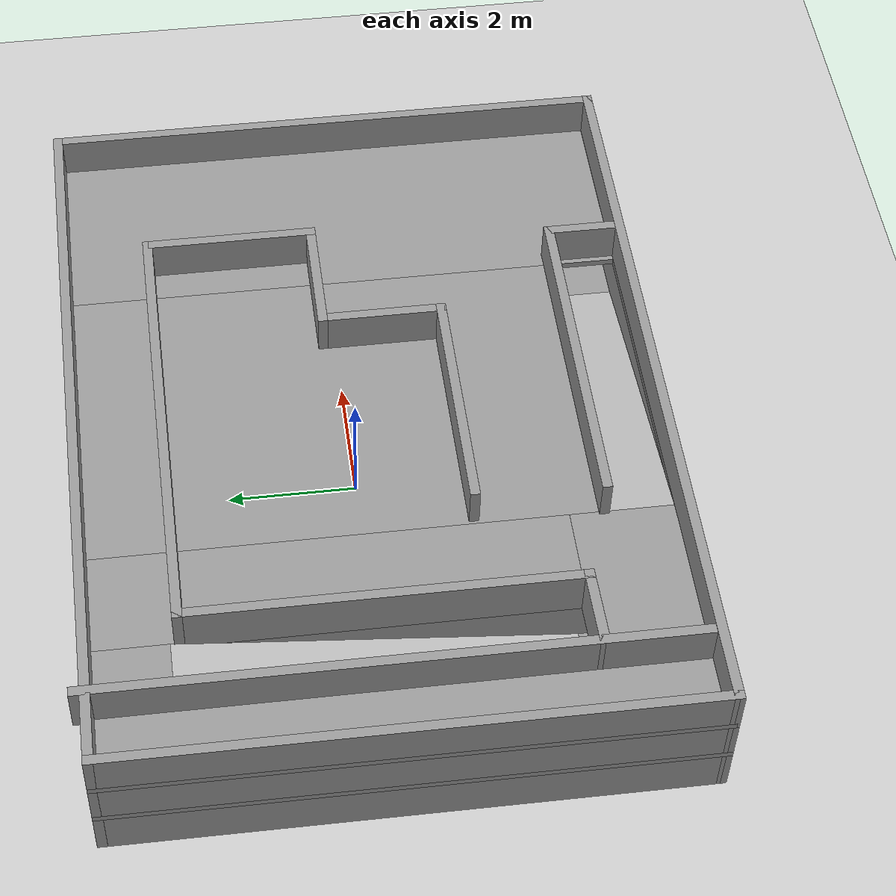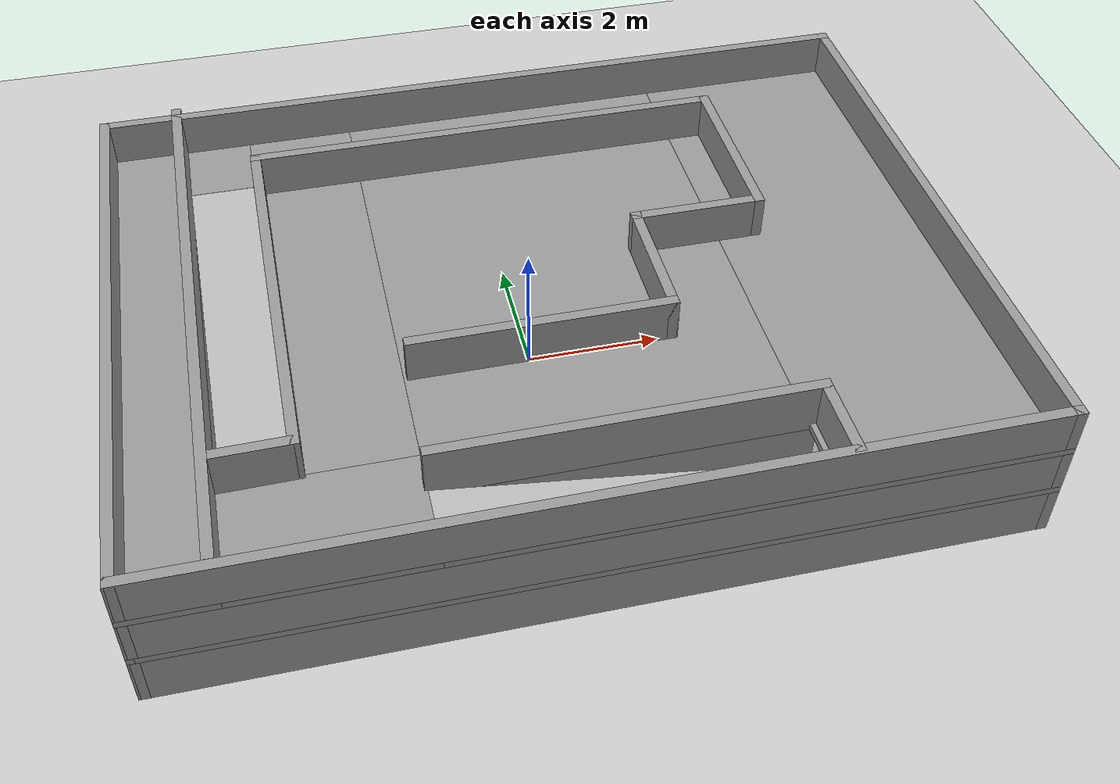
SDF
<sdf version="1.7">
 <world name="default">
  <light name="sun" type="directional">
   <pose>0 0 10 0 -0 0</pose>
   <diffuse>0.8 0.8 0.8 1</diffuse>
   <specular>0.2 0.2 0.2 1</specular>
   <attenuation>
    <range>1000</range>
    <constant>0.9</constant>
    <linear>0.01</linear>
    <quadratic>0.001</quadratic>
   </attenuation>
   <direction>-0.5 0.1 -0.9</direction>
   <spot><inner_angle>0</inner_angle><outer_angle>0</outer_angle><falloff>0</falloff></spot>
  </light>
  <model name="slope">
   <static>1</static>
   <pose>-4.15271 0.094007 1.1727 0 -0.126025 1.5708</pose>
   <link name="link">
    <collision name="collision"><geometry><box><size>6 1 0.1</size></box></geometry></collision>
    <visual name="visual"><geometry><box><size>6 1 0.1</size></box></geometry></visual>
   </link>
  </model>
  <model name="ground_plane">
   <static>1</static>
   <link name="link">
    <collision name="collision">
     <geometry><plane><normal>0 0 1</normal><size>100 100</size></plane></geometry>
     <surface>
      <contact><collide_bitmask>65535</collide_bitmask></contact>
      <friction><ode><mu>100</mu><mu2>50</mu2></ode></friction>
     </surface>
    </collision>
    <visual name="visual">
     <cast_shadows>0</cast_shadows>
     <geometry><plane><normal>0 0 1</normal><size>100 100</size></plane></geometry>
     <material>
      <script><uri>file://media/materials/scripts/gazebo.material</uri><name>Gazebo/Grey</name></script>
     </material>
    </visual>
   </link>
  </model>
  <gravity>0 0 -9.8</gravity>
  <magnetic_field>6e-06 2.3e-05 -4.2e-05</magnetic_field>
  <atmosphere type="adiabatic"/>
  <physics type="ode">
   <max_step_size>0.001</max_step_size>
   <real_time_factor>1</real_time_factor>
   <real_time_update_rate>1000</real_time_update_rate>
  </physics>
  <scene><ambient>0.4 0.4 0.4 1</ambient><background>0.7 0.7 0.7 1</background><shadows>1</shadows></scene>
  <spherical_coordinates>
   <surface_model>EARTH_WGS84</surface_model>
   <latitude_deg>0</latitude_deg>
   <longitude_deg>0</longitude_deg>
   <elevation>0</elevation>
   <heading_deg>0</heading_deg>
  </spherical_coordinates>
  <model name="building2">
   <pose>0.104983 -0.148677 0 0 -0 0</pose>
   <link name="Floor_0">
    <pose>-7.7e-05 -0.025995 0.75 0 -0 0</pose>
    <visual name="Floor_0_Visual_0">
     <pose>-5.9416 0 0.05 0 -0 0</pose>
     <geometry><box><size>0.099817 9.00002 0.1</size></box></geometry>
     <material>
      <script><uri>file://media/materials/scripts/gazebo.material</uri><name>Gazebo/Grey</name></script>
      <ambient>1 1 1 1</ambient>
     </material>
     <meta><layer>1</layer></meta>
    </visual>
    <collision name="Floor_0_Collision_0">
     <geometry><box><size>0.099817 9.00002 0.1</size></box></geometry>
     <pose>-5.9416 0 0.05 0 -0 0</pose>
    </collision>
    <visual name="Floor_0_Visual_1">
     <pose>0.049909 -3.73004 0.05 0 -0 0</pose>
     <geometry><box><size>11.8832 1.53994 0.1</size></box></geometry>
     <material>
      <script><uri>file://media/materials/scripts/gazebo.material</uri><name>Gazebo/Grey</name></script>
      <ambient>1 1 1 1</ambient>
     </material>
     <meta><layer>1</layer></meta>
    </visual>
    <collision name="Floor_0_Collision_1">
     <geometry><box><size>11.8832 1.53994 0.1</size></box></geometry>
     <pose>0.049909 -3.73004 0.05 0 -0 0</pose>
    </collision>
    <visual name="Floor_0_Visual_2">
     <pose>-0.039381 0.769968 0.05 0 -0 0</pose>
     <geometry><box><size>9.70461 7.46008 0.1</size></box></geometry>
     <material>
      <script><uri>file://media/materials/scripts/gazebo.material</uri><name>Gazebo/Grey</name></script>
      <ambient>1 1 1 1</ambient>
     </material>
     <meta><layer>1</layer></meta>
    </visual>
    <collision name="Floor_0_Collision_2">
     <geometry><box><size>9.70461 7.46008 0.1</size></box></geometry>
     <pose>-0.039381 0.769968 0.05 0 -0 0</pose>
    </collision>
    <visual name="Floor_0_Visual_3">
     <pose>5.40221 -2.86649 0.05 0 -0 0</pose>
     <geometry><box><size>1.17858 0.187166 0.1</size></box></geometry>
     <material>
      <script><uri>file://media/materials/scripts/gazebo.material</uri><name>Gazebo/Grey</name></script>
      <ambient>1 1 1 1</ambient>
     </material>
     <meta><layer>1</layer></meta>
    </visual>
    <collision name="Floor_0_Collision_3">
     <geometry><box><size>1.17858 0.187166 0.1</size></box></geometry>
     <pose>5.40221 -2.86649 0.05 0 -0 0</pose>
    </collision>
    <visual name="Floor_0_Visual_4">
     <pose>5.90221 0.863551 0.05 0 -0 0</pose>
     <geometry><box><size>0.178579 7.27292 0.1</size></box></geometry>
     <material>
      <script><uri>file://media/materials/scripts/gazebo.material</uri><name>Gazebo/Grey</name></script>
      <ambient>1 1 1 1</ambient>
     </material>
     <meta><layer>1</layer></meta>
    </visual>
    <collision name="Floor_0_Collision_4">
     <geometry><box><size>0.178579 7.27292 0.1</size></box></geometry>
     <pose>5.90221 0.863551 0.05 0 -0 0</pose>
    </collision>
    <visual name="Floor_0_Visual_5">
     <pose>-5.39169 3.76997 0.05 0 -0 0</pose>
     <geometry><box><size>1 1.46008 0.1</size></box></geometry>
     <material>
      <script><uri>file://media/materials/scripts/gazebo.material</uri><name>Gazebo/Grey</name></script>
      <ambient>1 1 1 1</ambient>
     </material>
     <meta><layer>1</layer></meta>
    </visual>
    <collision name="Floor_0_Collision_5">
     <geometry><box><size>1 1.46008 0.1</size></box></geometry>
     <pose>-5.39169 3.76997 0.05 0 -0 0</pose>
    </collision>
    <visual name="Floor_0_Visual_6">
     <pose>5.31292 3.86355 0.05 0 -0 0</pose>
     <geometry><box><size>1 1.27292 0.1</size></box></geometry>
     <material>
      <script><uri>file://media/materials/scripts/gazebo.material</uri><name>Gazebo/Grey</name></script>
      <ambient>1 1 1 1</ambient>
     </material>
     <meta><layer>1</layer></meta>
    </visual>
    <collision name="Floor_0_Collision_6">
     <geometry><box><size>1 1.27292 0.1</size></box></geometry>
     <pose>5.31292 3.86355 0.05 0 -0 0</pose>
    </collision>
   </link>
   <link name="Floor_1">
    <pose>-7.7e-05 -0.025995 1.5 0 -0 0</pose>
    <visual name="Floor_1_Visual_0">
     <pose>-5.37778 0 0.05 0 -0 0</pose>
     <geometry><box><size>1.22744 9.00002 0.1</size></box></geometry>
     <material>
      <script><uri>file://media/materials/scripts/gazebo.material</uri><name>Gazebo/Grey</name></script>
      <ambient>1 1 1 1</ambient>
     </material>
     <meta><layer>2</layer></meta>
    </visual>
    <collision name="Floor_1_Collision_0">
     <geometry><box><size>1.22744 9.00002 0.1</size></box></geometry>
     <pose>-5.37778 0 0.05 0 -0 0</pose>
    </collision>
    <visual name="Floor_1_Visual_1">
     <pose>-3.46371 -3.63629 0.05 0 -0 0</pose>
     <geometry><box><size>2.6007 1.72744 0.1</size></box></geometry>
     <material>
      <script><uri>file://media/materials/scripts/gazebo.material</uri><name>Gazebo/Grey</name></script>
      <ambient>1 1 1 1</ambient>
     </material>
     <meta><layer>2</layer></meta>
    </visual>
    <collision name="Floor_1_Collision_1">
     <geometry><box><size>2.6007 1.72744 0.1</size></box></geometry>
     <pose>-3.46371 -3.63629 0.05 0 -0 0</pose>
    </collision>
    <visual name="Floor_1_Visual_2">
     <pose>1.91407 -4.42405 0.05 0 -0 0</pose>
     <geometry><box><size>8.15487 0.151917 0.1</size></box></geometry>
     <material>
      <script><uri>file://media/materials/scripts/gazebo.material</uri><name>Gazebo/Grey</name></script>
      <ambient>1 1 1 1</ambient>
     </material>
     <meta><layer>2</layer></meta>
    </visual>
    <collision name="Floor_1_Collision_2">
     <geometry><box><size>8.15487 0.151917 0.1</size></box></geometry>
     <pose>1.91407 -4.42405 0.05 0 -0 0</pose>
    </collision>
    <visual name="Floor_1_Visual_3">
     <pose>4.41407 0.075959 0.05 0 -0 0</pose>
     <geometry><box><size>3.15487 8.8481 0.1</size></box></geometry>
     <material>
      <script><uri>file://media/materials/scripts/gazebo.material</uri><name>Gazebo/Grey</name></script>
      <ambient>1 1 1 1</ambient>
     </material>
     <meta><layer>2</layer></meta>
    </visual>
    <collision name="Floor_1_Collision_3">
     <geometry><box><size>3.15487 8.8481 0.1</size></box></geometry>
     <pose>4.41407 0.075959 0.05 0 -0 0</pose>
    </collision>
    <visual name="Floor_1_Visual_4">
     <pose>0.336637 0.575959 0.05 0 -0 0</pose>
     <geometry><box><size>5 7.8481 0.1</size></box></geometry>
     <material>
      <script><uri>file://media/materials/scripts/gazebo.material</uri><name>Gazebo/Grey</name></script>
      <ambient>1 1 1 1</ambient>
     </material>
     <meta><layer>2</layer></meta>
    </visual>
    <collision name="Floor_1_Collision_4">
     <geometry><box><size>5 7.8481 0.1</size></box></geometry>
     <pose>0.336637 0.575959 0.05 0 -0 0</pose>
    </collision>
    <visual name="Floor_1_Visual_5">
     <pose>-2.96371 0.863722 0.05 0 -0 0</pose>
     <geometry><box><size>1.6007 7.27257 0.1</size></box></geometry>
     <material>
      <script><uri>file://media/materials/scripts/gazebo.material</uri><name>Gazebo/Grey</name></script>
      <ambient>1 1 1 1</ambient>
     </material>
     <meta><layer>2</layer></meta>
    </visual>
    <collision name="Floor_1_Collision_5">
     <geometry><box><size>1.6007 7.27257 0.1</size></box></geometry>
     <pose>-2.96371 0.863722 0.05 0 -0 0</pose>
    </collision>
    <visual name="Floor_1_Visual_6">
     <pose>-4.26406 3.86372 0.05 0 -0 0</pose>
     <geometry><box><size>1 1.27257 0.1</size></box></geometry>
     <material>
      <script><uri>file://media/materials/scripts/gazebo.material</uri><name>Gazebo/Grey</name></script>
      <ambient>1 1 1 1</ambient>
     </material>
     <meta><layer>2</layer></meta>
    </visual>
    <collision name="Floor_1_Collision_6">
     <geometry><box><size>1 1.27257 0.1</size></box></geometry>
     <pose>-4.26406 3.86372 0.05 0 -0 0</pose>
    </collision>
   </link>
   <link name="Stairs_1">
    <visual name="Stairs_1_Visual_0">
     <pose>-5.39176 2.86393 0.01875 0 -0 0</pose>
     <geometry><box><size>1 0.3 0.0375</size></box></geometry>
     <material>
      <script><uri>file://media/materials/scripts/gazebo.material</uri><name>Gazebo/Grey</name></script>
      <ambient>1 1 1 1</ambient>
     </material>
     <meta><layer>0</layer></meta>
    </visual>
    <collision name="Stairs_1_Collision_0">
     <geometry><box><size>1 0.3 0.0375</size></box></geometry>
     <pose>-5.39176 2.86393 0.01875 0 -0 0</pose>
    </collision>
    <visual name="Stairs_1_Visual_1">
     <pose>-5.39176 2.56393 0.05625 0 -0 0</pose>
     <geometry><box><size>1 0.3 0.0375</size></box></geometry>
     <material>
      <script><uri>file://media/materials/scripts/gazebo.material</uri><name>Gazebo/Grey</name></script>
      <ambient>1 1 1 1</ambient>
     </material>
     <meta><layer>0</layer></meta>
    </visual>
    <collision name="Stairs_1_Collision_1">
     <geometry><box><size>1 0.3 0.0375</size></box></geometry>
     <pose>-5.39176 2.56393 0.05625 0 -0 0</pose>
    </collision>
    <visual name="Stairs_1_Visual_2">
     <pose>-5.39176 2.26393 0.09375 0 -0 0</pose>
     <geometry><box><size>1 0.3 0.0375</size></box></geometry>
     <material>
      <script><uri>file://media/materials/scripts/gazebo.material</uri><name>Gazebo/Grey</name></script>
      <ambient>1 1 1 1</ambient>
     </material>
     <meta><layer>0</layer></meta>
    </visual>
    <collision name="Stairs_1_Collision_2">
     <geometry><box><size>1 0.3 0.0375</size></box></geometry>
     <pose>-5.39176 2.26393 0.09375 0 -0 0</pose>
    </collision>
    <visual name="Stairs_1_Visual_3">
     <pose>-5.39176 1.96393 0.13125 0 -0 0</pose>
     <geometry><box><size>1 0.3 0.0375</size></box></geometry>
     <material>
      <script><uri>file://media/materials/scripts/gazebo.material</uri><name>Gazebo/Grey</name></script>
      <ambient>1 1 1 1</ambient>
     </material>
     <meta><layer>0</layer></meta>
    </visual>
    <collision name="Stairs_1_Collision_3">
     <geometry><box><size>1 0.3 0.0375</size></box></geometry>
     <pose>-5.39176 1.96393 0.13125 0 -0 0</pose>
    </collision>
    <visual name="Stairs_1_Visual_4">
     <pose>-5.39176 1.66393 0.16875 0 -0 0</pose>
     <geometry><box><size>1 0.3 0.0375</size></box></geometry>
     <material>
      <script><uri>file://media/materials/scripts/gazebo.material</uri><name>Gazebo/Grey</name></script>
      <ambient>1 1 1 1</ambient>
     </material>
     <meta><layer>0</layer></meta>
    </visual>
    <collision name="Stairs_1_Collision_4">
     <geometry><box><size>1 0.3 0.0375</size></box></geometry>
     <pose>-5.39176 1.66393 0.16875 0 -0 0</pose>
    </collision>
    <visual name="Stairs_1_Visual_5">
     <pose>-5.39176 1.36393 0.20625 0 -0 0</pose>
     <geometry><box><size>1 0.3 0.0375</size></box></geometry>
     <material>
      <script><uri>file://media/materials/scripts/gazebo.material</uri><name>Gazebo/Grey</name></script>
      <ambient>1 1 1 1</ambient>
     </material>
     <meta><layer>0</layer></meta>
    </visual>
    <collision name="Stairs_1_Collision_5">
     <geometry><box><size>1 0.3 0.0375</size></box></geometry>
     <pose>-5.39176 1.36393 0.20625 0 -0 0</pose>
    </collision>
    <visual name="Stairs_1_Visual_6">
     <pose>-5.39176 1.06393 0.24375 0 -0 0</pose>
     <geometry><box><size>1 0.3 0.0375</size></box></geometry>
     <material>
      <script><uri>file://media/materials/scripts/gazebo.material</uri><name>Gazebo/Grey</name></script>
      <ambient>1 1 1 1</ambient>
     </material>
     <meta><layer>0</layer></meta>
    </visual>
    <collision name="Stairs_1_Collision_6">
     <geometry><box><size>1 0.3 0.0375</size></box></geometry>
     <pose>-5.39176 1.06393 0.24375 0 -0 0</pose>
    </collision>
    <visual name="Stairs_1_Visual_7">
     <pose>-5.39176 0.763932 0.28125 0 -0 0</pose>
     <geometry><box><size>1 0.3 0.0375</size></box></geometry>
     <material>
      <script><uri>file://media/materials/scripts/gazebo.material</uri><name>Gazebo/Grey</name></script>
      <ambient>1 1 1 1</ambient>
     </material>
     <meta><layer>0</layer></meta>
    </visual>
    <collision name="Stairs_1_Collision_7">
     <geometry><box><size>1 0.3 0.0375</size></box></geometry>
     <pose>-5.39176 0.763932 0.28125 0 -0 0</pose>
    </collision>
    <visual name="Stairs_1_Visual_8">
     <pose>-5.39176 0.463932 0.31875 0 -0 0</pose>
     <geometry><box><size>1 0.3 0.0375</size></box></geometry>
     <material>
      <script><uri>file://media/materials/scripts/gazebo.material</uri><name>Gazebo/Grey</name></script>
      <ambient>1 1 1 1</ambient>
     </material>
     <meta><layer>0</layer></meta>
    </visual>
    <collision name="Stairs_1_Collision_8">
     <geometry><box><size>1 0.3 0.0375</size></box></geometry>
     <pose>-5.39176 0.463932 0.31875 0 -0 0</pose>
    </collision>
    <visual name="Stairs_1_Visual_9">
     <pose>-5.39176 0.163932 0.35625 0 -0 0</pose>
     <geometry><box><size>1 0.3 0.0375</size></box></geometry>
     <material>
      <script><uri>file://media/materials/scripts/gazebo.material</uri><name>Gazebo/Grey</name></script>
      <ambient>1 1 1 1</ambient>
     </material>
     <meta><layer>0</layer></meta>
    </visual>
    <collision name="Stairs_1_Collision_9">
     <geometry><box><size>1 0.3 0.0375</size></box></geometry>
     <pose>-5.39176 0.163932 0.35625 0 -0 0</pose>
    </collision>
    <visual name="Stairs_1_Visual_10">
     <pose>-5.39176 -0.136068 0.39375 0 -0 0</pose>
     <geometry><box><size>1 0.3 0.0375</size></box></geometry>
     <material>
      <script><uri>file://media/materials/scripts/gazebo.material</uri><name>Gazebo/Grey</name></script>
      <ambient>1 1 1 1</ambient>
     </material>
     <meta><layer>0</layer></meta>
    </visual>
    <collision name="Stairs_1_Collision_10">
     <geometry><box><size>1 0.3 0.0375</size></box></geometry>
     <pose>-5.39176 -0.136068 0.39375 0 -0 0</pose>
    </collision>
    <visual name="Stairs_1_Visual_11">
     <pose>-5.39176 -0.436068 0.43125 0 -0 0</pose>
     <geometry><box><size>1 0.3 0.0375</size></box></geometry>
     <material>
      <script><uri>file://media/materials/scripts/gazebo.material</uri><name>Gazebo/Grey</name></script>
      <ambient>1 1 1 1</ambient>
     </material>
     <meta><layer>0</layer></meta>
    </visual>
    <collision name="Stairs_1_Collision_11">
     <geometry><box><size>1 0.3 0.0375</size></box></geometry>
     <pose>-5.39176 -0.436068 0.43125 0 -0 0</pose>
    </collision>
    <visual name="Stairs_1_Visual_12">
     <pose>-5.39176 -0.736068 0.46875 0 -0 0</pose>
     <geometry><box><size>1 0.3 0.0375</size></box></geometry>
     <material>
      <script><uri>file://media/materials/scripts/gazebo.material</uri><name>Gazebo/Grey</name></script>
      <ambient>1 1 1 1</ambient>
     </material>
     <meta><layer>0</layer></meta>
    </visual>
    <collision name="Stairs_1_Collision_12">
     <geometry><box><size>1 0.3 0.0375</size></box></geometry>
     <pose>-5.39176 -0.736068 0.46875 0 -0 0</pose>
    </collision>
    <visual name="Stairs_1_Visual_13">
     <pose>-5.39176 -1.03607 0.50625 0 -0 0</pose>
     <geometry><box><size>1 0.3 0.0375</size></box></geometry>
     <material>
      <script><uri>file://media/materials/scripts/gazebo.material</uri><name>Gazebo/Grey</name></script>
      <ambient>1 1 1 1</ambient>
     </material>
     <meta><layer>0</layer></meta>
    </visual>
    <collision name="Stairs_1_Collision_13">
     <geometry><box><size>1 0.3 0.0375</size></box></geometry>
     <pose>-5.39176 -1.03607 0.50625 0 -0 0</pose>
    </collision>
    <visual name="Stairs_1_Visual_14">
     <pose>-5.39176 -1.33607 0.54375 0 -0 0</pose>
     <geometry><box><size>1 0.3 0.0375</size></box></geometry>
     <material>
      <script><uri>file://media/materials/scripts/gazebo.material</uri><name>Gazebo/Grey</name></script>
      <ambient>1 1 1 1</ambient>
     </material>
     <meta><layer>0</layer></meta>
    </visual>
    <collision name="Stairs_1_Collision_14">
     <geometry><box><size>1 0.3 0.0375</size></box></geometry>
     <pose>-5.39176 -1.33607 0.54375 0 -0 0</pose>
    </collision>
    <visual name="Stairs_1_Visual_15">
     <pose>-5.39176 -1.63607 0.58125 0 -0 0</pose>
     <geometry><box><size>1 0.3 0.0375</size></box></geometry>
     <material>
      <script><uri>file://media/materials/scripts/gazebo.material</uri><name>Gazebo/Grey</name></script>
      <ambient>1 1 1 1</ambient>
     </material>
     <meta><layer>0</layer></meta>
    </visual>
    <collision name="Stairs_1_Collision_15">
     <geometry><box><size>1 0.3 0.0375</size></box></geometry>
     <pose>-5.39176 -1.63607 0.58125 0 -0 0</pose>
    </collision>
    <visual name="Stairs_1_Visual_16">
     <pose>-5.39176 -1.93607 0.61875 0 -0 0</pose>
     <geometry><box><size>1 0.3 0.0375</size></box></geometry>
     <material>
      <script><uri>file://media/materials/scripts/gazebo.material</uri><name>Gazebo/Grey</name></script>
      <ambient>1 1 1 1</ambient>
     </material>
     <meta><layer>0</layer></meta>
    </visual>
    <collision name="Stairs_1_Collision_16">
     <geometry><box><size>1 0.3 0.0375</size></box></geometry>
     <pose>-5.39176 -1.93607 0.61875 0 -0 0</pose>
    </collision>
    <visual name="Stairs_1_Visual_17">
     <pose>-5.39176 -2.23607 0.65625 0 -0 0</pose>
     <geometry><box><size>1 0.3 0.0375</size></box></geometry>
     <material>
      <script><uri>file://media/materials/scripts/gazebo.material</uri><name>Gazebo/Grey</name></script>
      <ambient>1 1 1 1</ambient>
     </material>
     <meta><layer>0</layer></meta>
    </visual>
    <collision name="Stairs_1_Collision_17">
     <geometry><box><size>1 0.3 0.0375</size></box></geometry>
     <pose>-5.39176 -2.23607 0.65625 0 -0 0</pose>
    </collision>
    <visual name="Stairs_1_Visual_18">
     <pose>-5.39176 -2.53607 0.69375 0 -0 0</pose>
     <geometry><box><size>1 0.3 0.0375</size></box></geometry>
     <material>
      <script><uri>file://media/materials/scripts/gazebo.material</uri><name>Gazebo/Grey</name></script>
      <ambient>1 1 1 1</ambient>
     </material>
     <meta><layer>0</layer></meta>
    </visual>
    <collision name="Stairs_1_Collision_18">
     <geometry><box><size>1 0.3 0.0375</size></box></geometry>
     <pose>-5.39176 -2.53607 0.69375 0 -0 0</pose>
    </collision>
    <visual name="Stairs_1_Visual_19">
     <pose>-5.39176 -2.83607 0.73125 0 -0 0</pose>
     <geometry><box><size>1 0.3 0.0375</size></box></geometry>
     <material>
      <script><uri>file://media/materials/scripts/gazebo.material</uri><name>Gazebo/Grey</name></script>
      <ambient>1 1 1 1</ambient>
     </material>
     <meta><layer>0</layer></meta>
    </visual>
    <collision name="Stairs_1_Collision_19">
     <geometry><box><size>1 0.3 0.0375</size></box></geometry>
     <pose>-5.39176 -2.83607 0.73125 0 -0 0</pose>
    </collision>
   </link>
   <link name="Stairs_3">
    <visual name="Stairs_3_Visual_0">
     <pose>5.31285 -2.6489 0.01875 0 -0 -3.14159</pose>
     <geometry><box><size>1 0.3 0.0375</size></box></geometry>
     <material>
      <script><uri>file://media/materials/scripts/gazebo.material</uri><name>Gazebo/Grey</name></script>
      <ambient>1 1 1 1</ambient>
     </material>
     <meta><layer>0</layer></meta>
    </visual>
    <collision name="Stairs_3_Collision_0">
     <geometry><box><size>1 0.3 0.0375</size></box></geometry>
     <pose>5.31285 -2.6489 0.01875 0 -0 -3.14159</pose>
    </collision>
    <visual name="Stairs_3_Visual_1">
     <pose>5.31285 -2.3489 0.05625 0 -0 -3.14159</pose>
     <geometry><box><size>1 0.3 0.0375</size></box></geometry>
     <material>
      <script><uri>file://media/materials/scripts/gazebo.material</uri><name>Gazebo/Grey</name></script>
      <ambient>1 1 1 1</ambient>
     </material>
     <meta><layer>0</layer></meta>
    </visual>
    <collision name="Stairs_3_Collision_1">
     <geometry><box><size>1 0.3 0.0375</size></box></geometry>
     <pose>5.31285 -2.3489 0.05625 0 -0 -3.14159</pose>
    </collision>
    <visual name="Stairs_3_Visual_2">
     <pose>5.31285 -2.0489 0.09375 0 -0 -3.14159</pose>
     <geometry><box><size>1 0.3 0.0375</size></box></geometry>
     <material>
      <script><uri>file://media/materials/scripts/gazebo.material</uri><name>Gazebo/Grey</name></script>
      <ambient>1 1 1 1</ambient>
     </material>
     <meta><layer>0</layer></meta>
    </visual>
    <collision name="Stairs_3_Collision_2">
     <geometry><box><size>1 0.3 0.0375</size></box></geometry>
     <pose>5.31285 -2.0489 0.09375 0 -0 -3.14159</pose>
    </collision>
    <visual name="Stairs_3_Visual_3">
     <pose>5.31285 -1.7489 0.13125 0 -0 -3.14159</pose>
     <geometry><box><size>1 0.3 0.0375</size></box></geometry>
     <material>
      <script><uri>file://media/materials/scripts/gazebo.material</uri><name>Gazebo/Grey</name></script>
      <ambient>1 1 1 1</ambient>
     </material>
     <meta><layer>0</layer></meta>
    </visual>
    <collision name="Stairs_3_Collision_3">
     <geometry><box><size>1 0.3 0.0375</size></box></geometry>
     <pose>5.31285 -1.7489 0.13125 0 -0 -3.14159</pose>
    </collision>
    <visual name="Stairs_3_Visual_4">
     <pose>5.31285 -1.4489 0.16875 0 -0 -3.14159</pose>
     <geometry><box><size>1 0.3 0.0375</size></box></geometry>
     <material>
      <script><uri>file://media/materials/scripts/gazebo.material</uri><name>Gazebo/Grey</name></script>
      <ambient>1 1 1 1</ambient>
     </material>
     <meta><layer>0</layer></meta>
    </visual>
    <collision name="Stairs_3_Collision_4">
     <geometry><box><size>1 0.3 0.0375</size></box></geometry>
     <pose>5.31285 -1.4489 0.16875 0 -0 -3.14159</pose>
    </collision>
    <visual name="Stairs_3_Visual_5">
     <pose>5.31285 -1.1489 0.20625 0 -0 -3.14159</pose>
     <geometry><box><size>1 0.3 0.0375</size></box></geometry>
     <material>
      <script><uri>file://media/materials/scripts/gazebo.material</uri><name>Gazebo/Grey</name></script>
      <ambient>1 1 1 1</ambient>
     </material>
     <meta><layer>0</layer></meta>
    </visual>
    <collision name="Stairs_3_Collision_5">
     <geometry><box><size>1 0.3 0.0375</size></box></geometry>
     <pose>5.31285 -1.1489 0.20625 0 -0 -3.14159</pose>
    </collision>
    <visual name="Stairs_3_Visual_6">
     <pose>5.31285 -0.848902 0.24375 0 -0 -3.14159</pose>
     <geometry><box><size>1 0.3 0.0375</size></box></geometry>
     <material>
      <script><uri>file://media/materials/scripts/gazebo.material</uri><name>Gazebo/Grey</name></script>
      <ambient>1 1 1 1</ambient>
     </material>
     <meta><layer>0</layer></meta>
    </visual>
    <collision name="Stairs_3_Collision_6">
     <geometry><box><size>1 0.3 0.0375</size></box></geometry>
     <pose>5.31285 -0.848902 0.24375 0 -0 -3.14159</pose>
    </collision>
    <visual name="Stairs_3_Visual_7">
     <pose>5.31285 -0.548902 0.28125 0 -0 -3.14159</pose>
     <geometry><box><size>1 0.3 0.0375</size></box></geometry>
     <material>
      <script><uri>file://media/materials/scripts/gazebo.material</uri><name>Gazebo/Grey</name></script>
      <ambient>1 1 1 1</ambient>
     </material>
     <meta><layer>0</layer></meta>
    </visual>
    <collision name="Stairs_3_Collision_7">
     <geometry><box><size>1 0.3 0.0375</size></box></geometry>
     <pose>5.31285 -0.548902 0.28125 0 -0 -3.14159</pose>
    </collision>
    <visual name="Stairs_3_Visual_8">
     <pose>5.31285 -0.248901 0.31875 0 -0 -3.14159</pose>
     <geometry><box><size>1 0.3 0.0375</size></box></geometry>
     <material>
      <script><uri>file://media/materials/scripts/gazebo.material</uri><name>Gazebo/Grey</name></script>
      <ambient>1 1 1 1</ambient>
     </material>
     <meta><layer>0</layer></meta>
    </visual>
    <collision name="Stairs_3_Collision_8">
     <geometry><box><size>1 0.3 0.0375</size></box></geometry>
     <pose>5.31285 -0.248901 0.31875 0 -0 -3.14159</pose>
    </collision>
    <visual name="Stairs_3_Visual_9">
     <pose>5.31285 0.051098 0.35625 0 -0 -3.14159</pose>
     <geometry><box><size>1 0.3 0.0375</size></box></geometry>
     <material>
      <script><uri>file://media/materials/scripts/gazebo.material</uri><name>Gazebo/Grey</name></script>
      <ambient>1 1 1 1</ambient>
     </material>
     <meta><layer>0</layer></meta>
    </visual>
    <collision name="Stairs_3_Collision_9">
     <geometry><box><size>1 0.3 0.0375</size></box></geometry>
     <pose>5.31285 0.051098 0.35625 0 -0 -3.14159</pose>
    </collision>
    <visual name="Stairs_3_Visual_10">
     <pose>5.31285 0.351099 0.39375 0 -0 -3.14159</pose>
     <geometry><box><size>1 0.3 0.0375</size></box></geometry>
     <material>
      <script><uri>file://media/materials/scripts/gazebo.material</uri><name>Gazebo/Grey</name></script>
      <ambient>1 1 1 1</ambient>
     </material>
     <meta><layer>0</layer></meta>
    </visual>
    <collision name="Stairs_3_Collision_10">
     <geometry><box><size>1 0.3 0.0375</size></box></geometry>
     <pose>5.31285 0.351099 0.39375 0 -0 -3.14159</pose>
    </collision>
    <visual name="Stairs_3_Visual_11">
     <pose>5.31285 0.651098 0.43125 0 -0 -3.14159</pose>
     <geometry><box><size>1 0.3 0.0375</size></box></geometry>
     <material>
      <script><uri>file://media/materials/scripts/gazebo.material</uri><name>Gazebo/Grey</name></script>
      <ambient>1 1 1 1</ambient>
     </material>
     <meta><layer>0</layer></meta>
    </visual>
    <collision name="Stairs_3_Collision_11">
     <geometry><box><size>1 0.3 0.0375</size></box></geometry>
     <pose>5.31285 0.651098 0.43125 0 -0 -3.14159</pose>
    </collision>
    <visual name="Stairs_3_Visual_12">
     <pose>5.31285 0.951098 0.46875 0 -0 -3.14159</pose>
     <geometry><box><size>1 0.3 0.0375</size></box></geometry>
     <material>
      <script><uri>file://media/materials/scripts/gazebo.material</uri><name>Gazebo/Grey</name></script>
      <ambient>1 1 1 1</ambient>
     </material>
     <meta><layer>0</layer></meta>
    </visual>
    <collision name="Stairs_3_Collision_12">
     <geometry><box><size>1 0.3 0.0375</size></box></geometry>
     <pose>5.31285 0.951098 0.46875 0 -0 -3.14159</pose>
    </collision>
    <visual name="Stairs_3_Visual_13">
     <pose>5.31285 1.2511 0.50625 0 -0 -3.14159</pose>
     <geometry><box><size>1 0.3 0.0375</size></box></geometry>
     <material>
      <script><uri>file://media/materials/scripts/gazebo.material</uri><name>Gazebo/Grey</name></script>
      <ambient>1 1 1 1</ambient>
     </material>
     <meta><layer>0</layer></meta>
    </visual>
    <collision name="Stairs_3_Collision_13">
     <geometry><box><size>1 0.3 0.0375</size></box></geometry>
     <pose>5.31285 1.2511 0.50625 0 -0 -3.14159</pose>
    </collision>
    <visual name="Stairs_3_Visual_14">
     <pose>5.31285 1.5511 0.54375 0 -0 -3.14159</pose>
     <geometry><box><size>1 0.3 0.0375</size></box></geometry>
     <material>
      <script><uri>file://media/materials/scripts/gazebo.material</uri><name>Gazebo/Grey</name></script>
      <ambient>1 1 1 1</ambient>
     </material>
     <meta><layer>0</layer></meta>
    </visual>
    <collision name="Stairs_3_Collision_14">
     <geometry><box><size>1 0.3 0.0375</size></box></geometry>
     <pose>5.31285 1.5511 0.54375 0 -0 -3.14159</pose>
    </collision>
    <visual name="Stairs_3_Visual_15">
     <pose>5.31285 1.8511 0.58125 0 -0 -3.14159</pose>
     <geometry><box><size>1 0.3 0.0375</size></box></geometry>
     <material>
      <script><uri>file://media/materials/scripts/gazebo.material</uri><name>Gazebo/Grey</name></script>
      <ambient>1 1 1 1</ambient>
     </material>
     <meta><layer>0</layer></meta>
    </visual>
    <collision name="Stairs_3_Collision_15">
     <geometry><box><size>1 0.3 0.0375</size></box></geometry>
     <pose>5.31285 1.8511 0.58125 0 -0 -3.14159</pose>
    </collision>
    <visual name="Stairs_3_Visual_16">
     <pose>5.31285 2.1511 0.61875 0 -0 -3.14159</pose>
     <geometry><box><size>1 0.3 0.0375</size></box></geometry>
     <material>
      <script><uri>file://media/materials/scripts/gazebo.material</uri><name>Gazebo/Grey</name></script>
      <ambient>1 1 1 1</ambient>
     </material>
     <meta><layer>0</layer></meta>
    </visual>
    <collision name="Stairs_3_Collision_16">
     <geometry><box><size>1 0.3 0.0375</size></box></geometry>
     <pose>5.31285 2.1511 0.61875 0 -0 -3.14159</pose>
    </collision>
    <visual name="Stairs_3_Visual_17">
     <pose>5.31285 2.4511 0.65625 0 -0 -3.14159</pose>
     <geometry><box><size>1 0.3 0.0375</size></box></geometry>
     <material>
      <script><uri>file://media/materials/scripts/gazebo.material</uri><name>Gazebo/Grey</name></script>
      <ambient>1 1 1 1</ambient>
     </material>
     <meta><layer>0</layer></meta>
    </visual>
    <collision name="Stairs_3_Collision_17">
     <geometry><box><size>1 0.3 0.0375</size></box></geometry>
     <pose>5.31285 2.4511 0.65625 0 -0 -3.14159</pose>
    </collision>
    <visual name="Stairs_3_Visual_18">
     <pose>5.31285 2.7511 0.69375 0 -0 -3.14159</pose>
     <geometry><box><size>1 0.3 0.0375</size></box></geometry>
     <material>
      <script><uri>file://media/materials/scripts/gazebo.material</uri><name>Gazebo/Grey</name></script>
      <ambient>1 1 1 1</ambient>
     </material>
     <meta><layer>0</layer></meta>
    </visual>
    <collision name="Stairs_3_Collision_18">
     <geometry><box><size>1 0.3 0.0375</size></box></geometry>
     <pose>5.31285 2.7511 0.69375 0 -0 -3.14159</pose>
    </collision>
    <visual name="Stairs_3_Visual_19">
     <pose>5.31285 3.0511 0.73125 0 -0 -3.14159</pose>
     <geometry><box><size>1 0.3 0.0375</size></box></geometry>
     <material>
      <script><uri>file://media/materials/scripts/gazebo.material</uri><name>Gazebo/Grey</name></script>
      <ambient>1 1 1 1</ambient>
     </material>
     <meta><layer>0</layer></meta>
    </visual>
    <collision name="Stairs_3_Collision_19">
     <geometry><box><size>1 0.3 0.0375</size></box></geometry>
     <pose>5.31285 3.0511 0.73125 0 -0 -3.14159</pose>
    </collision>
   </link>
   <link name="Stairs_5">
    <visual name="Stairs_5_Visual_0">
     <pose>-4.26414 -2.64856 0.76875 0 -0 -3.14159</pose>
     <geometry><box><size>1 0.3 0.0375</size></box></geometry>
     <material>
      <script><uri>file://media/materials/scripts/gazebo.material</uri><name>Gazebo/Grey</name></script>
      <ambient>1 1 1 1</ambient>
     </material>
     <meta><layer>1</layer></meta>
    </visual>
    <collision name="Stairs_5_Collision_0">
     <geometry><box><size>1 0.3 0.0375</size></box></geometry>
     <pose>-4.26414 -2.64856 0.76875 0 -0 -3.14159</pose>
    </collision>
    <visual name="Stairs_5_Visual_1">
     <pose>-4.26414 -2.34856 0.80625 0 -0 -3.14159</pose>
     <geometry><box><size>1 0.3 0.0375</size></box></geometry>
     <material>
      <script><uri>file://media/materials/scripts/gazebo.material</uri><name>Gazebo/Grey</name></script>
      <ambient>1 1 1 1</ambient>
     </material>
     <meta><layer>1</layer></meta>
    </visual>
    <collision name="Stairs_5_Collision_1">
     <geometry><box><size>1 0.3 0.0375</size></box></geometry>
     <pose>-4.26414 -2.34856 0.80625 0 -0 -3.14159</pose>
    </collision>
    <visual name="Stairs_5_Visual_2">
     <pose>-4.26414 -2.04856 0.84375 0 -0 -3.14159</pose>
     <geometry><box><size>1 0.3 0.0375</size></box></geometry>
     <material>
      <script><uri>file://media/materials/scripts/gazebo.material</uri><name>Gazebo/Grey</name></script>
      <ambient>1 1 1 1</ambient>
     </material>
     <meta><layer>1</layer></meta>
    </visual>
    <collision name="Stairs_5_Collision_2">
     <geometry><box><size>1 0.3 0.0375</size></box></geometry>
     <pose>-4.26414 -2.04856 0.84375 0 -0 -3.14159</pose>
    </collision>
    <visual name="Stairs_5_Visual_3">
     <pose>-4.26414 -1.74856 0.88125 0 -0 -3.14159</pose>
     <geometry><box><size>1 0.3 0.0375</size></box></geometry>
     <material>
      <script><uri>file://media/materials/scripts/gazebo.material</uri><name>Gazebo/Grey</name></script>
      <ambient>1 1 1 1</ambient>
     </material>
     <meta><layer>1</layer></meta>
    </visual>
    <collision name="Stairs_5_Collision_3">
     <geometry><box><size>1 0.3 0.0375</size></box></geometry>
     <pose>-4.26414 -1.74856 0.88125 0 -0 -3.14159</pose>
    </collision>
    <visual name="Stairs_5_Visual_4">
     <pose>-4.26414 -1.44856 0.91875 0 -0 -3.14159</pose>
     <geometry><box><size>1 0.3 0.0375</size></box></geometry>
     <material>
      <script><uri>file://media/materials/scripts/gazebo.material</uri><name>Gazebo/Grey</name></script>
      <ambient>1 1 1 1</ambient>
     </material>
     <meta><layer>1</layer></meta>
    </visual>
    <collision name="Stairs_5_Collision_4">
     <geometry><box><size>1 0.3 0.0375</size></box></geometry>
     <pose>-4.26414 -1.44856 0.91875 0 -0 -3.14159</pose>
    </collision>
    <visual name="Stairs_5_Visual_5">
     <pose>-4.26414 -1.14856 0.95625 0 -0 -3.14159</pose>
     <geometry><box><size>1 0.3 0.0375</size></box></geometry>
     <material>
      <script><uri>file://media/materials/scripts/gazebo.material</uri><name>Gazebo/Grey</name></script>
      <ambient>1 1 1 1</ambient>
     </material>
     <meta><layer>1</layer></meta>
    </visual>
    <collision name="Stairs_5_Collision_5">
     <geometry><box><size>1 0.3 0.0375</size></box></geometry>
     <pose>-4.26414 -1.14856 0.95625 0 -0 -3.14159</pose>
    </collision>
    <visual name="Stairs_5_Visual_6">
     <pose>-4.26414 -0.84856 0.99375 0 -0 -3.14159</pose>
     <geometry><box><size>1 0.3 0.0375</size></box></geometry>
     <material>
      <script><uri>file://media/materials/scripts/gazebo.material</uri><name>Gazebo/Grey</name></script>
      <ambient>1 1 1 1</ambient>
     </material>
     <meta><layer>1</layer></meta>
    </visual>
    <collision name="Stairs_5_Collision_6">
     <geometry><box><size>1 0.3 0.0375</size></box></geometry>
     <pose>-4.26414 -0.84856 0.99375 0 -0 -3.14159</pose>
    </collision>
    <visual name="Stairs_5_Visual_7">
     <pose>-4.26414 -0.548561 1.03125 0 -0 -3.14159</pose>
     <geometry><box><size>1 0.3 0.0375</size></box></geometry>
     <material>
      <script><uri>file://media/materials/scripts/gazebo.material</uri><name>Gazebo/Grey</name></script>
      <ambient>1 1 1 1</ambient>
     </material>
     <meta><layer>1</layer></meta>
    </visual>
    <collision name="Stairs_5_Collision_7">
     <geometry><box><size>1 0.3 0.0375</size></box></geometry>
     <pose>-4.26414 -0.548561 1.03125 0 -0 -3.14159</pose>
    </collision>
    <visual name="Stairs_5_Visual_8">
     <pose>-4.26414 -0.24856 1.06875 0 -0 -3.14159</pose>
     <geometry><box><size>1 0.3 0.0375</size></box></geometry>
     <material>
      <script><uri>file://media/materials/scripts/gazebo.material</uri><name>Gazebo/Grey</name></script>
      <ambient>1 1 1 1</ambient>
     </material>
     <meta><layer>1</layer></meta>
    </visual>
    <collision name="Stairs_5_Collision_8">
     <geometry><box><size>1 0.3 0.0375</size></box></geometry>
     <pose>-4.26414 -0.24856 1.06875 0 -0 -3.14159</pose>
    </collision>
    <visual name="Stairs_5_Visual_9">
     <pose>-4.26414 0.051439 1.10625 0 -0 -3.14159</pose>
     <geometry><box><size>1 0.3 0.0375</size></box></geometry>
     <material>
      <script><uri>file://media/materials/scripts/gazebo.material</uri><name>Gazebo/Grey</name></script>
      <ambient>1 1 1 1</ambient>
     </material>
     <meta><layer>1</layer></meta>
    </visual>
    <collision name="Stairs_5_Collision_9">
     <geometry><box><size>1 0.3 0.0375</size></box></geometry>
     <pose>-4.26414 0.051439 1.10625 0 -0 -3.14159</pose>
    </collision>
    <visual name="Stairs_5_Visual_10">
     <pose>-4.26414 0.351439 1.14375 0 -0 -3.14159</pose>
     <geometry><box><size>1 0.3 0.0375</size></box></geometry>
     <material>
      <script><uri>file://media/materials/scripts/gazebo.material</uri><name>Gazebo/Grey</name></script>
      <ambient>1 1 1 1</ambient>
     </material>
     <meta><layer>1</layer></meta>
    </visual>
    <collision name="Stairs_5_Collision_10">
     <geometry><box><size>1 0.3 0.0375</size></box></geometry>
     <pose>-4.26414 0.351439 1.14375 0 -0 -3.14159</pose>
    </collision>
    <visual name="Stairs_5_Visual_11">
     <pose>-4.26414 0.651439 1.18125 0 -0 -3.14159</pose>
     <geometry><box><size>1 0.3 0.0375</size></box></geometry>
     <material>
      <script><uri>file://media/materials/scripts/gazebo.material</uri><name>Gazebo/Grey</name></script>
      <ambient>1 1 1 1</ambient>
     </material>
     <meta><layer>1</layer></meta>
    </visual>
    <collision name="Stairs_5_Collision_11">
     <geometry><box><size>1 0.3 0.0375</size></box></geometry>
     <pose>-4.26414 0.651439 1.18125 0 -0 -3.14159</pose>
    </collision>
    <visual name="Stairs_5_Visual_12">
     <pose>-4.26414 0.951439 1.21875 0 -0 -3.14159</pose>
     <geometry><box><size>1 0.3 0.0375</size></box></geometry>
     <material>
      <script><uri>file://media/materials/scripts/gazebo.material</uri><name>Gazebo/Grey</name></script>
      <ambient>1 1 1 1</ambient>
     </material>
     <meta><layer>1</layer></meta>
    </visual>
    <collision name="Stairs_5_Collision_12">
     <geometry><box><size>1 0.3 0.0375</size></box></geometry>
     <pose>-4.26414 0.951439 1.21875 0 -0 -3.14159</pose>
    </collision>
    <visual name="Stairs_5_Visual_13">
     <pose>-4.26414 1.25144 1.25625 0 -0 -3.14159</pose>
     <geometry><box><size>1 0.3 0.0375</size></box></geometry>
     <material>
      <script><uri>file://media/materials/scripts/gazebo.material</uri><name>Gazebo/Grey</name></script>
      <ambient>1 1 1 1</ambient>
     </material>
     <meta><layer>1</layer></meta>
    </visual>
    <collision name="Stairs_5_Collision_13">
     <geometry><box><size>1 0.3 0.0375</size></box></geometry>
     <pose>-4.26414 1.25144 1.25625 0 -0 -3.14159</pose>
    </collision>
    <visual name="Stairs_5_Visual_14">
     <pose>-4.26414 1.55144 1.29375 0 -0 -3.14159</pose>
     <geometry><box><size>1 0.3 0.0375</size></box></geometry>
     <material>
      <script><uri>file://media/materials/scripts/gazebo.material</uri><name>Gazebo/Grey</name></script>
      <ambient>1 1 1 1</ambient>
     </material>
     <meta><layer>1</layer></meta>
    </visual>
    <collision name="Stairs_5_Collision_14">
     <geometry><box><size>1 0.3 0.0375</size></box></geometry>
     <pose>-4.26414 1.55144 1.29375 0 -0 -3.14159</pose>
    </collision>
    <visual name="Stairs_5_Visual_15">
     <pose>-4.26414 1.85144 1.33125 0 -0 -3.14159</pose>
     <geometry><box><size>1 0.3 0.0375</size></box></geometry>
     <material>
      <script><uri>file://media/materials/scripts/gazebo.material</uri><name>Gazebo/Grey</name></script>
      <ambient>1 1 1 1</ambient>
     </material>
     <meta><layer>1</layer></meta>
    </visual>
    <collision name="Stairs_5_Collision_15">
     <geometry><box><size>1 0.3 0.0375</size></box></geometry>
     <pose>-4.26414 1.85144 1.33125 0 -0 -3.14159</pose>
    </collision>
    <visual name="Stairs_5_Visual_16">
     <pose>-4.26414 2.15144 1.36875 0 -0 -3.14159</pose>
     <geometry><box><size>1 0.3 0.0375</size></box></geometry>
     <material>
      <script><uri>file://media/materials/scripts/gazebo.material</uri><name>Gazebo/Grey</name></script>
      <ambient>1 1 1 1</ambient>
     </material>
     <meta><layer>1</layer></meta>
    </visual>
    <collision name="Stairs_5_Collision_16">
     <geometry><box><size>1 0.3 0.0375</size></box></geometry>
     <pose>-4.26414 2.15144 1.36875 0 -0 -3.14159</pose>
    </collision>
    <visual name="Stairs_5_Visual_17">
     <pose>-4.26414 2.45144 1.40625 0 -0 -3.14159</pose>
     <geometry><box><size>1 0.3 0.0375</size></box></geometry>
     <material>
      <script><uri>file://media/materials/scripts/gazebo.material</uri><name>Gazebo/Grey</name></script>
      <ambient>1 1 1 1</ambient>
     </material>
     <meta><layer>1</layer></meta>
    </visual>
    <collision name="Stairs_5_Collision_17">
     <geometry><box><size>1 0.3 0.0375</size></box></geometry>
     <pose>-4.26414 2.45144 1.40625 0 -0 -3.14159</pose>
    </collision>
    <visual name="Stairs_5_Visual_18">
     <pose>-4.26414 2.75144 1.44375 0 -0 -3.14159</pose>
     <geometry><box><size>1 0.3 0.0375</size></box></geometry>
     <material>
      <script><uri>file://media/materials/scripts/gazebo.material</uri><name>Gazebo/Grey</name></script>
      <ambient>1 1 1 1</ambient>
     </material>
     <meta><layer>1</layer></meta>
    </visual>
    <collision name="Stairs_5_Collision_18">
     <geometry><box><size>1 0.3 0.0375</size></box></geometry>
     <pose>-4.26414 2.75144 1.44375 0 -0 -3.14159</pose>
    </collision>
    <visual name="Stairs_5_Visual_19">
     <pose>-4.26414 3.05144 1.48125 0 -0 -3.14159</pose>
     <geometry><box><size>1 0.3 0.0375</size></box></geometry>
     <material>
      <script><uri>file://media/materials/scripts/gazebo.material</uri><name>Gazebo/Grey</name></script>
      <ambient>1 1 1 1</ambient>
     </material>
     <meta><layer>1</layer></meta>
    </visual>
    <collision name="Stairs_5_Collision_19">
     <geometry><box><size>1 0.3 0.0375</size></box></geometry>
     <pose>-4.26414 3.05144 1.48125 0 -0 -3.14159</pose>
    </collision>
   </link>
   <link name="Stairs_6">
    <visual name="Stairs_6_Visual_0">
     <pose>2.66989 -3.87409 0.775 0 -0 -1.5708</pose>
     <geometry><box><size>1 0.333333 0.05</size></box></geometry>
     <material>
      <script><uri>file://media/materials/scripts/gazebo.material</uri><name>Gazebo/Grey</name></script>
      <ambient>1 1 1 1</ambient>
     </material>
     <meta><layer>1</layer></meta>
    </visual>
    <collision name="Stairs_6_Collision_0">
     <geometry><box><size>1 0.333333 0.05</size></box></geometry>
     <pose>2.66989 -3.87409 0.775 0 -0 -1.5708</pose>
    </collision>
    <visual name="Stairs_6_Visual_1">
     <pose>2.33656 -3.87409 0.825 0 -0 -1.5708</pose>
     <geometry><box><size>1 0.333333 0.05</size></box></geometry>
     <material>
      <script><uri>file://media/materials/scripts/gazebo.material</uri><name>Gazebo/Grey</name></script>
      <ambient>1 1 1 1</ambient>
     </material>
     <meta><layer>1</layer></meta>
    </visual>
    <collision name="Stairs_6_Collision_1">
     <geometry><box><size>1 0.333333 0.05</size></box></geometry>
     <pose>2.33656 -3.87409 0.825 0 -0 -1.5708</pose>
    </collision>
    <visual name="Stairs_6_Visual_2">
     <pose>2.00323 -3.87409 0.875 0 -0 -1.5708</pose>
     <geometry><box><size>1 0.333333 0.05</size></box></geometry>
     <material>
      <script><uri>file://media/materials/scripts/gazebo.material</uri><name>Gazebo/Grey</name></script>
      <ambient>1 1 1 1</ambient>
     </material>
     <meta><layer>1</layer></meta>
    </visual>
    <collision name="Stairs_6_Collision_2">
     <geometry><box><size>1 0.333333 0.05</size></box></geometry>
     <pose>2.00323 -3.87409 0.875 0 -0 -1.5708</pose>
    </collision>
    <visual name="Stairs_6_Visual_3">
     <pose>1.66989 -3.87409 0.925 0 -0 -1.5708</pose>
     <geometry><box><size>1 0.333333 0.05</size></box></geometry>
     <material>
      <script><uri>file://media/materials/scripts/gazebo.material</uri><name>Gazebo/Grey</name></script>
      <ambient>1 1 1 1</ambient>
     </material>
     <meta><layer>1</layer></meta>
    </visual>
    <collision name="Stairs_6_Collision_3">
     <geometry><box><size>1 0.333333 0.05</size></box></geometry>
     <pose>1.66989 -3.87409 0.925 0 -0 -1.5708</pose>
    </collision>
    <visual name="Stairs_6_Visual_4">
     <pose>1.33656 -3.87409 0.975 0 -0 -1.5708</pose>
     <geometry><box><size>1 0.333333 0.05</size></box></geometry>
     <material>
      <script><uri>file://media/materials/scripts/gazebo.material</uri><name>Gazebo/Grey</name></script>
      <ambient>1 1 1 1</ambient>
     </material>
     <meta><layer>1</layer></meta>
    </visual>
    <collision name="Stairs_6_Collision_4">
     <geometry><box><size>1 0.333333 0.05</size></box></geometry>
     <pose>1.33656 -3.87409 0.975 0 -0 -1.5708</pose>
    </collision>
    <visual name="Stairs_6_Visual_5">
     <pose>1.00323 -3.87409 1.025 0 -0 -1.5708</pose>
     <geometry><box><size>1 0.333333 0.05</size></box></geometry>
     <material>
      <script><uri>file://media/materials/scripts/gazebo.material</uri><name>Gazebo/Grey</name></script>
      <ambient>1 1 1 1</ambient>
     </material>
     <meta><layer>1</layer></meta>
    </visual>
    <collision name="Stairs_6_Collision_5">
     <geometry><box><size>1 0.333333 0.05</size></box></geometry>
     <pose>1.00323 -3.87409 1.025 0 -0 -1.5708</pose>
    </collision>
    <visual name="Stairs_6_Visual_6">
     <pose>0.669893 -3.87409 1.075 0 -0 -1.5708</pose>
     <geometry><box><size>1 0.333333 0.05</size></box></geometry>
     <material>
      <script><uri>file://media/materials/scripts/gazebo.material</uri><name>Gazebo/Grey</name></script>
      <ambient>1 1 1 1</ambient>
     </material>
     <meta><layer>1</layer></meta>
    </visual>
    <collision name="Stairs_6_Collision_6">
     <geometry><box><size>1 0.333333 0.05</size></box></geometry>
     <pose>0.669893 -3.87409 1.075 0 -0 -1.5708</pose>
    </collision>
    <visual name="Stairs_6_Visual_7">
     <pose>0.33656 -3.87409 1.125 0 -0 -1.5708</pose>
     <geometry><box><size>1 0.333333 0.05</size></box></geometry>
     <material>
      <script><uri>file://media/materials/scripts/gazebo.material</uri><name>Gazebo/Grey</name></script>
      <ambient>1 1 1 1</ambient>
     </material>
     <meta><layer>1</layer></meta>
    </visual>
    <collision name="Stairs_6_Collision_7">
     <geometry><box><size>1 0.333333 0.05</size></box></geometry>
     <pose>0.33656 -3.87409 1.125 0 -0 -1.5708</pose>
    </collision>
    <visual name="Stairs_6_Visual_8">
     <pose>0.003226 -3.87409 1.175 0 -0 -1.5708</pose>
     <geometry><box><size>1 0.333333 0.05</size></box></geometry>
     <material>
      <script><uri>file://media/materials/scripts/gazebo.material</uri><name>Gazebo/Grey</name></script>
      <ambient>1 1 1 1</ambient>
     </material>
     <meta><layer>1</layer></meta>
    </visual>
    <collision name="Stairs_6_Collision_8">
     <geometry><box><size>1 0.333333 0.05</size></box></geometry>
     <pose>0.003226 -3.87409 1.175 0 -0 -1.5708</pose>
    </collision>
    <visual name="Stairs_6_Visual_9">
     <pose>-0.330107 -3.87409 1.225 0 -0 -1.5708</pose>
     <geometry><box><size>1 0.333333 0.05</size></box></geometry>
     <material>
      <script><uri>file://media/materials/scripts/gazebo.material</uri><name>Gazebo/Grey</name></script>
      <ambient>1 1 1 1</ambient>
     </material>
     <meta><layer>1</layer></meta>
    </visual>
    <collision name="Stairs_6_Collision_9">
     <geometry><box><size>1 0.333333 0.05</size></box></geometry>
     <pose>-0.330107 -3.87409 1.225 0 -0 -1.5708</pose>
    </collision>
    <visual name="Stairs_6_Visual_10">
     <pose>-0.66344 -3.87409 1.275 0 -0 -1.5708</pose>
     <geometry><box><size>1 0.333333 0.05</size></box></geometry>
     <material>
      <script><uri>file://media/materials/scripts/gazebo.material</uri><name>Gazebo/Grey</name></script>
      <ambient>1 1 1 1</ambient>
     </material>
     <meta><layer>1</layer></meta>
    </visual>
    <collision name="Stairs_6_Collision_10">
     <geometry><box><size>1 0.333333 0.05</size></box></geometry>
     <pose>-0.66344 -3.87409 1.275 0 -0 -1.5708</pose>
    </collision>
    <visual name="Stairs_6_Visual_11">
     <pose>-0.996774 -3.87409 1.325 0 -0 -1.5708</pose>
     <geometry><box><size>1 0.333333 0.05</size></box></geometry>
     <material>
      <script><uri>file://media/materials/scripts/gazebo.material</uri><name>Gazebo/Grey</name></script>
      <ambient>1 1 1 1</ambient>
     </material>
     <meta><layer>1</layer></meta>
    </visual>
    <collision name="Stairs_6_Collision_11">
     <geometry><box><size>1 0.333333 0.05</size></box></geometry>
     <pose>-0.996774 -3.87409 1.325 0 -0 -1.5708</pose>
    </collision>
    <visual name="Stairs_6_Visual_12">
     <pose>-1.33011 -3.87409 1.375 0 -0 -1.5708</pose>
     <geometry><box><size>1 0.333333 0.05</size></box></geometry>
     <material>
      <script><uri>file://media/materials/scripts/gazebo.material</uri><name>Gazebo/Grey</name></script>
      <ambient>1 1 1 1</ambient>
     </material>
     <meta><layer>1</layer></meta>
    </visual>
    <collision name="Stairs_6_Collision_12">
     <geometry><box><size>1 0.333333 0.05</size></box></geometry>
     <pose>-1.33011 -3.87409 1.375 0 -0 -1.5708</pose>
    </collision>
    <visual name="Stairs_6_Visual_13">
     <pose>-1.66344 -3.87409 1.425 0 -0 -1.5708</pose>
     <geometry><box><size>1 0.333333 0.05</size></box></geometry>
     <material>
      <script><uri>file://media/materials/scripts/gazebo.material</uri><name>Gazebo/Grey</name></script>
      <ambient>1 1 1 1</ambient>
     </material>
     <meta><layer>1</layer></meta>
    </visual>
    <collision name="Stairs_6_Collision_13">
     <geometry><box><size>1 0.333333 0.05</size></box></geometry>
     <pose>-1.66344 -3.87409 1.425 0 -0 -1.5708</pose>
    </collision>
    <visual name="Stairs_6_Visual_14">
     <pose>-1.99677 -3.87409 1.475 0 -0 -1.5708</pose>
     <geometry><box><size>1 0.333333 0.05</size></box></geometry>
     <material>
      <script><uri>file://media/materials/scripts/gazebo.material</uri><name>Gazebo/Grey</name></script>
      <ambient>1 1 1 1</ambient>
     </material>
     <meta><layer>1</layer></meta>
    </visual>
    <collision name="Stairs_6_Collision_14">
     <geometry><box><size>1 0.333333 0.05</size></box></geometry>
     <pose>-1.99677 -3.87409 1.475 0 -0 -1.5708</pose>
    </collision>
   </link>
   <link name="Wall_0">
    <collision name="Wall_0_Collision">
     <geometry><box><size>9 0.15 0.75</size></box></geometry>
     <pose>0 0 0.375 0 -0 0</pose>
    </collision>
    <visual name="Wall_0_Visual">
     <pose>0 0 0.375 0 -0 0</pose>
     <geometry><box><size>9 0.15 0.75</size></box></geometry>
     <material>
      <script><uri>file://media/materials/scripts/gazebo.material</uri><name>Gazebo/Grey</name></script>
      <ambient>1 1 1 1</ambient>
     </material>
     <meta><layer>0</layer></meta>
    </visual>
    <pose>-5.91607 -0.025995 0 0 -0 -1.57091</pose>
   </link>
   <link name="Wall_1">
    <collision name="Wall_1_Collision">
     <geometry><box><size>11.983 0.15 0.75</size></box></geometry>
     <pose>0 0 0.375 0 -0 0</pose>
    </collision>
    <visual name="Wall_1_Visual">
     <pose>0 0 0.375 0 -0 0</pose>
     <geometry><box><size>11.983 0.15 0.75</size></box></geometry>
     <material>
      <script><uri>file://media/materials/scripts/gazebo.material</uri><name>Gazebo/Grey</name></script>
      <ambient>1 1 1 1</ambient>
     </material>
     <meta><layer>0</layer></meta>
    </visual>
    <pose>-7.3e-05 -4.45099 0 0 -0 0</pose>
   </link>
   <link name="Wall_10">
    <collision name="Wall_10_Collision">
     <geometry><box><size>6 0.15 0.75</size></box></geometry>
     <pose>0 0 0.375 0 -0 0</pose>
    </collision>
    <visual name="Wall_10_Visual">
     <pose>0 0 0.375 0 -0 0</pose>
     <geometry><box><size>6 0.15 0.75</size></box></geometry>
     <material>
      <script><uri>file://media/materials/scripts/gazebo.material</uri><name>Gazebo/Grey</name></script>
      <ambient>1 1 1 1</ambient>
     </material>
     <meta><layer>0</layer></meta>
    </visual>
    <pose>-0.963573 0.127005 0 0 -0 -1.5708</pose>
   </link>
   <link name="Wall_11">
    <collision name="Wall_11_Collision">
     <geometry><box><size>2 0.15 0.75</size></box></geometry>
     <pose>0 0 0.375 0 -0 0</pose>
    </collision>
    <visual name="Wall_11_Visual">
     <pose>0 0 0.375 0 -0 0</pose>
     <geometry><box><size>2 0.15 0.75</size></box></geometry>
     <material>
      <script><uri>file://media/materials/scripts/gazebo.material</uri><name>Gazebo/Grey</name></script>
      <ambient>1 1 1 1</ambient>
     </material>
     <meta><layer>0</layer></meta>
    </visual>
    <pose>-1.88857 -2.79799 0 0 -0 3.14159</pose>
   </link>
   <link name="Wall_13">
    <collision name="Wall_13_Collision">
     <geometry><box><size>3.5 0.15 0.75</size></box></geometry>
     <pose>0 0 0.375 0 -0 0</pose>
    </collision>
    <visual name="Wall_13_Visual">
     <pose>0 0 0.375 0 -0 0</pose>
     <geometry><box><size>3.5 0.15 0.75</size></box></geometry>
     <material>
      <script><uri>file://media/materials/scripts/gazebo.material</uri><name>Gazebo/Grey</name></script>
      <ambient>1 1 1 1</ambient>
     </material>
     <meta><layer>0</layer></meta>
    </visual>
    <pose>3.09543 2.98201 0 0 -0 3.14159</pose>
   </link>
   <link name="Wall_14">
    <collision name="Wall_14_Collision">
     <geometry><box><size>6 0.15 0.75</size></box></geometry>
     <pose>0 0 0.375 0 -0 0</pose>
    </collision>
    <visual name="Wall_14_Visual">
     <pose>0 0 0.375 0 -0 0</pose>
     <geometry><box><size>6 0.15 0.75</size></box></geometry>
     <material>
      <script><uri>file://media/materials/scripts/gazebo.material</uri><name>Gazebo/Grey</name></script>
      <ambient>1 1 1 1</ambient>
     </material>
     <meta><layer>0</layer></meta>
    </visual>
    <pose>1.42043 0.057005 0 0 -0 -1.5708</pose>
   </link>
   <link name="Wall_16">
    <collision name="Wall_16_Collision">
     <geometry><box><size>9 0.15 0.75</size></box></geometry>
     <pose>0 0 0.375 0 -0 0</pose>
    </collision>
    <visual name="Wall_16_Visual">
     <pose>0 0 0.375 0 -0 0</pose>
     <geometry><box><size>9 0.15 0.75</size></box></geometry>
     <material>
      <script><uri>file://media/materials/scripts/gazebo.material</uri><name>Gazebo/Grey</name></script>
      <ambient>1 1 1 1</ambient>
     </material>
     <meta><layer>1</layer></meta>
    </visual>
    <pose>-5.91607 -0.025995 0.75 0 -0 -1.57091</pose>
   </link>
   <link name="Wall_17">
    <collision name="Wall_17_Collision">
     <geometry><box><size>11.983 0.15 0.75</size></box></geometry>
     <pose>0 0 0.375 0 -0 0</pose>
    </collision>
    <visual name="Wall_17_Visual">
     <pose>0 0 0.375 0 -0 0</pose>
     <geometry><box><size>11.983 0.15 0.75</size></box></geometry>
     <material>
      <script><uri>file://media/materials/scripts/gazebo.material</uri><name>Gazebo/Grey</name></script>
      <ambient>1 1 1 1</ambient>
     </material>
     <meta><layer>1</layer></meta>
    </visual>
    <pose>-7.3e-05 -4.45099 0.75 0 -0 0</pose>
   </link>
   <link name="Wall_18">
    <collision name="Wall_18_Collision">
     <geometry><box><size>9 0.15 0.75</size></box></geometry>
     <pose>0 0 0.375 0 -0 0</pose>
    </collision>
    <visual name="Wall_18_Visual">
     <pose>0 0 0.375 0 -0 0</pose>
     <geometry><box><size>9 0.15 0.75</size></box></geometry>
     <material>
      <script><uri>file://media/materials/scripts/gazebo.material</uri><name>Gazebo/Grey</name></script>
      <ambient>1 1 1 1</ambient>
     </material>
     <meta><layer>1</layer></meta>
    </visual>
    <pose>5.91643 -0.025995 0.75 0 -0 1.5708</pose>
   </link>
   <link name="Wall_19">
    <collision name="Wall_19_Collision">
     <geometry><box><size>11.982 0.15 0.75</size></box></geometry>
     <pose>0 0 0.375 0 -0 0</pose>
    </collision>
    <visual name="Wall_19_Visual">
     <pose>0 0 0.375 0 -0 0</pose>
     <geometry><box><size>11.982 0.15 0.75</size></box></geometry>
     <material>
      <script><uri>file://media/materials/scripts/gazebo.material</uri><name>Gazebo/Grey</name></script>
      <ambient>1 1 1 1</ambient>
     </material>
     <meta><layer>1</layer></meta>
    </visual>
    <pose>0.000427 4.399 0.75 0 -0 3.14159</pose>
   </link>
   <link name="Wall_2">
    <collision name="Wall_2_Collision">
     <geometry><box><size>9 0.15 0.75</size></box></geometry>
     <pose>0 0 0.375 0 -0 0</pose>
    </collision>
    <visual name="Wall_2_Visual">
     <pose>0 0 0.375 0 -0 0</pose>
     <geometry><box><size>9 0.15 0.75</size></box></geometry>
     <material>
      <script><uri>file://media/materials/scripts/gazebo.material</uri><name>Gazebo/Grey</name></script>
      <ambient>1 1 1 1</ambient>
     </material>
     <meta><layer>0</layer></meta>
    </visual>
    <pose>5.91643 -0.025995 0 0 -0 1.5708</pose>
   </link>
   <link name="Wall_20">
    <collision name="Wall_20_Collision">
     <geometry><box><size>6 0.15 0.75</size></box></geometry>
     <pose>0 0 0.375 0 -0 0</pose>
    </collision>
    <visual name="Wall_20_Visual">
     <pose>0 0 0.375 0 -0 0</pose>
     <geometry><box><size>6 0.15 0.75</size></box></geometry>
     <material>
      <script><uri>file://media/materials/scripts/gazebo.material</uri><name>Gazebo/Grey</name></script>
      <ambient>1 1 1 1</ambient>
     </material>
     <meta><layer>1</layer></meta>
    </visual>
    <pose>-4.81357 0.127005 0.75 0 -0 -1.5708</pose>
   </link>
   <link name="Wall_21">
    <collision name="Wall_21_Collision">
     <geometry><box><size>6 0.15 0.75</size></box></geometry>
     <pose>0 0 0.375 0 -0 0</pose>
    </collision>
    <visual name="Wall_21_Visual">
     <pose>0 0 0.375 0 -0 0</pose>
     <geometry><box><size>6 0.15 0.75</size></box></geometry>
     <material>
      <script><uri>file://media/materials/scripts/gazebo.material</uri><name>Gazebo/Grey</name></script>
      <ambient>1 1 1 1</ambient>
     </material>
     <meta><layer>1</layer></meta>
    </visual>
    <pose>4.73543 0.057005 0.75 0 -0 -1.5708</pose>
   </link>
   <link name="Wall_27">
    <collision name="Wall_27_Collision">
     <geometry><box><size>1.25 0.15 0.75</size></box></geometry>
     <pose>0 0 0.375 0 -0 0</pose>
    </collision>
    <visual name="Wall_27_Visual">
     <pose>0 0 0.375 0 -0 0</pose>
     <geometry><box><size>1.25 0.15 0.75</size></box></geometry>
     <material>
      <script><uri>file://media/materials/scripts/gazebo.material</uri><name>Gazebo/Grey</name></script>
      <ambient>1 1 1 1</ambient>
     </material>
     <meta><layer>1</layer></meta>
    </visual>
    <pose>-5.36357 3.052 0.75 0 -0 3.14159</pose>
   </link>
   <link name="Wall_29">
    <collision name="Wall_29_Collision">
     <geometry><box><size>1.285 0.15 0.75</size></box></geometry>
     <pose>0 0 0.375 0 -0 0</pose>
    </collision>
    <visual name="Wall_29_Visual">
     <pose>0 0 0.375 0 -0 0</pose>
     <geometry><box><size>1.285 0.15 0.75</size></box></geometry>
     <material>
      <script><uri>file://media/materials/scripts/gazebo.material</uri><name>Gazebo/Grey</name></script>
      <ambient>1 1 1 1</ambient>
     </material>
     <meta><layer>1</layer></meta>
    </visual>
    <pose>5.30293 -2.868 0.75 0 -0 0</pose>
   </link>
   <link name="Wall_3">
    <collision name="Wall_3_Collision">
     <geometry><box><size>11.9823 0.15 0.75</size></box></geometry>
     <pose>0 0 0.375 0 -0 0</pose>
    </collision>
    <visual name="Wall_3_Visual">
     <pose>0 0 0.375 0 -0 0</pose>
     <geometry><box><size>11.9823 0.15 0.75</size></box></geometry>
     <material>
      <script><uri>file://media/materials/scripts/gazebo.material</uri><name>Gazebo/Grey</name></script>
      <ambient>1 1 1 1</ambient>
     </material>
     <meta><layer>0</layer></meta>
    </visual>
    <pose>0.000427 4.399 0 0 -0 3.14159</pose>
   </link>
   <link name="Wall_31">
    <collision name="Wall_31_Collision">
     <geometry><box><size>6 0.15 0.75</size></box></geometry>
     <pose>0 0 0.375 0 -0 0</pose>
    </collision>
    <visual name="Wall_31_Visual">
     <pose>0 0 0.375 0 -0 0</pose>
     <geometry><box><size>6 0.15 0.75</size></box></geometry>
     <material>
      <script><uri>file://media/materials/scripts/gazebo.material</uri><name>Gazebo/Grey</name></script>
      <ambient>1 1 1 1</ambient>
     </material>
     <meta><layer>1</layer></meta>
    </visual>
    <pose>-3.69457 0.144005 0.75 0 -0 -1.5708</pose>
   </link>
   <link name="Wall_33">
    <collision name="Wall_33_Collision">
     <geometry><box><size>5.25 0.15 0.75</size></box></geometry>
     <pose>0 0 0.375 0 -0 0</pose>
    </collision>
    <visual name="Wall_33_Visual">
     <pose>0 0 0.375 0 -0 0</pose>
     <geometry><box><size>5.25 0.15 0.75</size></box></geometry>
     <material>
      <script><uri>file://media/materials/scripts/gazebo.material</uri><name>Gazebo/Grey</name></script>
      <ambient>1 1 1 1</ambient>
     </material>
     <meta><layer>1</layer></meta>
    </visual>
    <pose>0.314427 -3.31399 0.75 0 -0 3.14159</pose>
   </link>
   <link name="Wall_38">
    <collision name="Wall_38_Collision">
     <geometry><box><size>2.715 0.15 0.75</size></box></geometry>
     <pose>0 0 0.375 0 -0 0</pose>
    </collision>
    <visual name="Wall_38_Visual">
     <pose>0 0 0.375 0 -0 0</pose>
     <geometry><box><size>2.715 0.15 0.75</size></box></geometry>
     <material>
      <script><uri>file://media/materials/scripts/gazebo.material</uri><name>Gazebo/Grey</name></script>
      <ambient>1 1 1 1</ambient>
     </material>
     <meta><layer>1</layer></meta>
    </visual>
    <pose>3.45293 2.98201 0.75 0 -0 3.14159</pose>
   </link>
   <link name="Wall_40">
    <collision name="Wall_40_Collision">
     <geometry><box><size>3.75 0.15 0.75</size></box></geometry>
     <pose>0 0 0.375 0 -0 0</pose>
    </collision>
    <visual name="Wall_40_Visual">
     <pose>0 0 0.375 0 -0 0</pose>
     <geometry><box><size>3.75 0.15 0.75</size></box></geometry>
     <material>
      <script><uri>file://media/materials/scripts/gazebo.material</uri><name>Gazebo/Grey</name></script>
      <ambient>1 1 1 1</ambient>
     </material>
     <meta><layer>1</layer></meta>
    </visual>
    <pose>2.86443 -1.51399 0.75 0 -0 1.5708</pose>
   </link>
   <link name="Wall_42">
    <collision name="Wall_42_Collision">
     <geometry><box><size>5.25 0.15 0.75</size></box></geometry>
     <pose>0 0 0.375 0 -0 0</pose>
    </collision>
    <visual name="Wall_42_Visual">
     <pose>0 0 0.375 0 -0 0</pose>
     <geometry><box><size>5.25 0.15 0.75</size></box></geometry>
     <material>
      <script><uri>file://media/materials/scripts/gazebo.material</uri><name>Gazebo/Grey</name></script>
      <ambient>1 1 1 1</ambient>
     </material>
     <meta><layer>1</layer></meta>
    </visual>
    <pose>0.314427 0.286005 0.75 0 -0 3.14159</pose>
   </link>
   <link name="Wall_43">
    <collision name="Wall_43_Collision">
     <geometry><box><size>2 0.15 0.75</size></box></geometry>
     <pose>0 0 0.375 0 -0 0</pose>
    </collision>
    <visual name="Wall_43_Visual">
     <pose>0 0 0.375 0 -0 0</pose>
     <geometry><box><size>2 0.15 0.75</size></box></geometry>
     <material>
      <script><uri>file://media/materials/scripts/gazebo.material</uri><name>Gazebo/Grey</name></script>
      <ambient>1 1 1 1</ambient>
     </material>
     <meta><layer>1</layer></meta>
    </visual>
    <pose>-2.23557 -0.638995 0.75 0 -0 -1.5708</pose>
   </link>
   <link name="Wall_45">
    <collision name="Wall_45_Collision">
     <geometry><box><size>9 0.15 0.75</size></box></geometry>
     <pose>0 0 0.375 0 -0 0</pose>
    </collision>
    <visual name="Wall_45_Visual">
     <pose>0 0 0.375 0 -0 0</pose>
     <geometry><box><size>9 0.15 0.75</size></box></geometry>
     <material>
      <script><uri>file://media/materials/scripts/gazebo.material</uri><name>Gazebo/Grey</name></script>
      <ambient>1 1 1 1</ambient>
     </material>
     <meta><layer>2</layer></meta>
    </visual>
    <pose>-5.91607 -0.025995 1.5 0 -0 -1.57091</pose>
   </link>
   <link name="Wall_46">
    <collision name="Wall_46_Collision">
     <geometry><box><size>11.983 0.15 0.75</size></box></geometry>
     <pose>0 0 0.375 0 -0 0</pose>
    </collision>
    <visual name="Wall_46_Visual">
     <pose>0 0 0.375 0 -0 0</pose>
     <geometry><box><size>11.983 0.15 0.75</size></box></geometry>
     <material>
      <script><uri>file://media/materials/scripts/gazebo.material</uri><name>Gazebo/Grey</name></script>
      <ambient>1 1 1 1</ambient>
     </material>
     <meta><layer>2</layer></meta>
    </visual>
    <pose>-7.3e-05 -4.45099 1.5 0 -0 0</pose>
   </link>
   <link name="Wall_47">
    <collision name="Wall_47_Collision">
     <geometry><box><size>9 0.15 0.75</size></box></geometry>
     <pose>0 0 0.375 0 -0 0</pose>
    </collision>
    <visual name="Wall_47_Visual">
     <pose>0 0 0.375 0 -0 0</pose>
     <geometry><box><size>9 0.15 0.75</size></box></geometry>
     <material>
      <script><uri>file://media/materials/scripts/gazebo.material</uri><name>Gazebo/Grey</name></script>
      <ambient>1 1 1 1</ambient>
     </material>
     <meta><layer>2</layer></meta>
    </visual>
    <pose>5.91643 -0.025995 1.5 0 -0 1.5708</pose>
   </link>
   <link name="Wall_48">
    <collision name="Wall_48_Collision">
     <geometry><box><size>11.982 0.15 0.75</size></box></geometry>
     <pose>0 0 0.375 0 -0 0</pose>
    </collision>
    <visual name="Wall_48_Visual">
     <pose>0 0 0.375 0 -0 0</pose>
     <geometry><box><size>11.982 0.15 0.75</size></box></geometry>
     <material>
      <script><uri>file://media/materials/scripts/gazebo.material</uri><name>Gazebo/Grey</name></script>
      <ambient>1 1 1 1</ambient>
     </material>
     <meta><layer>2</layer></meta>
    </visual>
    <pose>0.000427 4.399 1.5 0 -0 3.14159</pose>
   </link>
   <link name="Wall_49">
    <collision name="Wall_49_Collision">
     <geometry><box><size>9 0.15 0.75</size></box></geometry>
     <pose>0 0 0.375 0 -0 0</pose>
    </collision>
    <visual name="Wall_49_Visual">
     <pose>0 0 0.375 0 -0 0</pose>
     <geometry><box><size>9 0.15 0.75</size></box></geometry>
     <material>
      <script><uri>file://media/materials/scripts/gazebo.material</uri><name>Gazebo/Grey</name></script>
      <ambient>1 1 1 1</ambient>
     </material>
     <meta><layer>2</layer></meta>
    </visual>
    <pose>-4.81357 0.127005 1.5 0 -0 -1.5708</pose>
   </link>
   <link name="Wall_5">
    <collision name="Wall_5_Collision">
     <geometry><box><size>6 0.15 0.75</size></box></geometry>
     <pose>0 0 0.375 0 -0 0</pose>
    </collision>
    <visual name="Wall_5_Visual">
     <pose>0 0 0.375 0 -0 0</pose>
     <geometry><box><size>6 0.15 0.75</size></box></geometry>
     <material>
      <script><uri>file://media/materials/scripts/gazebo.material</uri><name>Gazebo/Grey</name></script>
      <ambient>1 1 1 1</ambient>
     </material>
     <meta><layer>0</layer></meta>
    </visual>
    <pose>-4.81357 0.127005 0 0 -0 -1.5708</pose>
   </link>
   <link name="Wall_53">
    <collision name="Wall_53_Collision">
     <geometry><box><size>6 0.15 0.75</size></box></geometry>
     <pose>0 0 0.375 0 -0 0</pose>
    </collision>
    <visual name="Wall_53_Visual">
     <pose>0 0 0.375 0 -0 0</pose>
     <geometry><box><size>6 0.15 0.75</size></box></geometry>
     <material>
      <script><uri>file://media/materials/scripts/gazebo.material</uri><name>Gazebo/Grey</name></script>
      <ambient>1 1 1 1</ambient>
     </material>
     <meta><layer>2</layer></meta>
    </visual>
    <pose>-3.69457 0.144005 1.5 0 -0 -1.5708</pose>
   </link>
   <link name="Wall_54">
    <collision name="Wall_54_Collision">
     <geometry><box><size>5.2766 0.15 0.75</size></box></geometry>
     <pose>0 0 0.375 0 -0 0</pose>
    </collision>
    <visual name="Wall_54_Visual">
     <pose>0 0 0.375 0 -0 0</pose>
     <geometry><box><size>5.2766 0.15 0.75</size></box></geometry>
     <material>
      <script><uri>file://media/materials/scripts/gazebo.material</uri><name>Gazebo/Grey</name></script>
      <ambient>1 1 1 1</ambient>
     </material>
     <meta><layer>2</layer></meta>
    </visual>
    <pose>0.430643 -3.31399 1.5 0 -0 3.14159</pose>
   </link>
   <link name="Wall_59">
    <collision name="Wall_59_Collision">
     <geometry><box><size>1.26913 0.15 0.75</size></box></geometry>
     <pose>0 0 0.375 0 -0 0</pose>
    </collision>
    <visual name="Wall_59_Visual">
     <pose>0 0 0.375 0 -0 0</pose>
     <geometry><box><size>1.26913 0.15 0.75</size></box></geometry>
     <material>
      <script><uri>file://media/materials/scripts/gazebo.material</uri><name>Gazebo/Grey</name></script>
      <ambient>1 1 1 1</ambient>
     </material>
     <meta><layer>2</layer></meta>
    </visual>
    <pose>-4.25407 -2.7895 1.5 0 -0 -3.1264</pose>
   </link>
   <link name="Wall_61">
    <collision name="Wall_61_Collision">
     <geometry><box><size>7.25 0.15 0.75</size></box></geometry>
     <pose>0 0 0.375 0 -0 0</pose>
    </collision>
    <visual name="Wall_61_Visual">
     <pose>0 0 0.375 0 -0 0</pose>
     <geometry><box><size>7.25 0.15 0.75</size></box></geometry>
     <material>
      <script><uri>file://media/materials/scripts/gazebo.material</uri><name>Gazebo/Grey</name></script>
      <ambient>1 1 1 1</ambient>
     </material>
     <meta><layer>2</layer></meta>
    </visual>
    <pose>-0.144573 3.06901 1.5 0 -0 0</pose>
   </link>
   <link name="Wall_66">
    <collision name="Wall_66_Collision">
     <geometry><box><size>2.75 0.15 0.75</size></box></geometry>
     <pose>0 0 0.375 0 -0 0</pose>
    </collision>
    <visual name="Wall_66_Visual">
     <pose>0 0 0.375 0 -0 0</pose>
     <geometry><box><size>2.75 0.15 0.75</size></box></geometry>
     <material>
      <script><uri>file://media/materials/scripts/gazebo.material</uri><name>Gazebo/Grey</name></script>
      <ambient>1 1 1 1</ambient>
     </material>
     <meta><layer>2</layer></meta>
    </visual>
    <pose>3.40543 1.769 1.5 0 -0 -1.5708</pose>
   </link>
   <link name="Wall_67">
    <collision name="Wall_67_Collision">
     <geometry><box><size>2 0.15 0.75</size></box></geometry>
     <pose>0 0 0.375 0 -0 0</pose>
    </collision>
    <visual name="Wall_67_Visual">
     <pose>0 0 0.375 0 -0 0</pose>
     <geometry><box><size>2 0.15 0.75</size></box></geometry>
     <material>
      <script><uri>file://media/materials/scripts/gazebo.material</uri><name>Gazebo/Grey</name></script>
      <ambient>1 1 1 1</ambient>
     </material>
     <meta><layer>2</layer></meta>
    </visual>
    <pose>2.48043 0.469005 1.5 0 -0 3.14159</pose>
   </link>
   <link name="Wall_68">
    <collision name="Wall_68_Collision">
     <geometry><box><size>2 0.15 0.75</size></box></geometry>
     <pose>0 0 0.375 0 -0 0</pose>
    </collision>
    <visual name="Wall_68_Visual">
     <pose>0 0 0.375 0 -0 0</pose>
     <geometry><box><size>2 0.15 0.75</size></box></geometry>
     <material>
      <script><uri>file://media/materials/scripts/gazebo.material</uri><name>Gazebo/Grey</name></script>
      <ambient>1 1 1 1</ambient>
     </material>
     <meta><layer>2</layer></meta>
    </visual>
    <pose>1.55543 -0.455995 1.5 0 -0 -1.5708</pose>
   </link>
   <link name="Wall_69">
    <collision name="Wall_69_Collision">
     <geometry><box><size>3.75 0.15 0.75</size></box></geometry>
     <pose>0 0 0.375 0 -0 0</pose>
    </collision>
    <visual name="Wall_69_Visual">
     <pose>0 0 0.375 0 -0 0</pose>
     <geometry><box><size>3.75 0.15 0.75</size></box></geometry>
     <material>
      <script><uri>file://media/materials/scripts/gazebo.material</uri><name>Gazebo/Grey</name></script>
      <ambient>1 1 1 1</ambient>
     </material>
     <meta><layer>2</layer></meta>
    </visual>
    <pose>-0.244573 -1.38099 1.5 0 -0 3.14159</pose>
   </link>
   <link name="Wall_7">
    <collision name="Wall_7_Collision">
     <geometry><box><size>6 0.15 0.75</size></box></geometry>
     <pose>0 0 0.375 0 -0 0</pose>
    </collision>
    <visual name="Wall_7_Visual">
     <pose>0 0 0.375 0 -0 0</pose>
     <geometry><box><size>6 0.15 0.75</size></box></geometry>
     <material>
      <script><uri>file://media/materials/scripts/gazebo.material</uri><name>Gazebo/Grey</name></script>
      <ambient>1 1 1 1</ambient>
     </material>
     <meta><layer>0</layer></meta>
    </visual>
    <pose>4.77043 0.057005 0 0 -0 -1.5708</pose>
   </link>
   <link name="Wall_71">
    <collision name="Wall_71_Collision">
     <geometry><box><size>1.25 0.15 0.75</size></box></geometry>
     <pose>0 0 0.375 0 -0 0</pose>
    </collision>
    <visual name="Wall_71_Visual">
     <pose>0 0 0.375 0 -0 0</pose>
     <geometry><box><size>1.25 0.15 0.75</size></box></geometry>
     <material>
      <script><uri>file://media/materials/scripts/gazebo.material</uri><name>Gazebo/Grey</name></script>
      <ambient>1 1 1 1</ambient>
     </material>
     <meta><layer>2</layer></meta>
    </visual>
    <pose>2.99394 -3.864 1.5 0 -0 -1.5708</pose>
   </link>
   <link name="Wall_9">
    <collision name="Wall_9_Collision">
     <geometry><box><size>4 0.15 0.75</size></box></geometry>
     <pose>0 0 0.375 0 -0 0</pose>
    </collision>
    <visual name="Wall_9_Visual">
     <pose>0 0 0.375 0 -0 0</pose>
     <geometry><box><size>4 0.15 0.75</size></box></geometry>
     <material>
      <script><uri>file://media/materials/scripts/gazebo.material</uri><name>Gazebo/Grey</name></script>
      <ambient>1 1 1 1</ambient>
     </material>
     <meta><layer>0</layer></meta>
    </visual>
    <pose>-2.88857 3.052 0 0 -0 0</pose>
   </link>
   <static>1</static>
  </model>
  <model name="slope_clone">
   <static>1</static>
   <pose>0.646481 -4.02506 1.14019 0 0.149022 0</pose>
   <link name="link">
    <collision name="collision"><geometry><box><size>5.5 1 0.1</size></box></geometry></collision>
    <visual name="visual"><geometry><box><size>5.5 1 0.1</size></box></geometry></visual>
   </link>
  </model>
  <model name="slope_clone_0">
   <static>1</static>
   <pose>5.41558 -0.160802 0.368928 0 -0.132978 1.5708</pose>
   <link name="link">
    <collision name="collision"><geometry><box><size>6.5 1 0.1</size></box></geometry></collision>
    <visual name="visual"><geometry><box><size>6.5 1 0.1</size></box></geometry></visual>
   </link>
  </model>
  <model name="slope_clone_1">
   <static>1</static>
   <pose>-5.28798 0.072601 0.363331 0 0.135024 1.5708</pose>
   <link name="link">
    <collision name="collision"><geometry><box><size>6.5 1 0.1</size></box></geometry></collision>
    <visual name="visual"><geometry><box><size>6.5 1 0.1</size></box></geometry></visual>
   </link>
  </model>
 </world>
</sdf>
